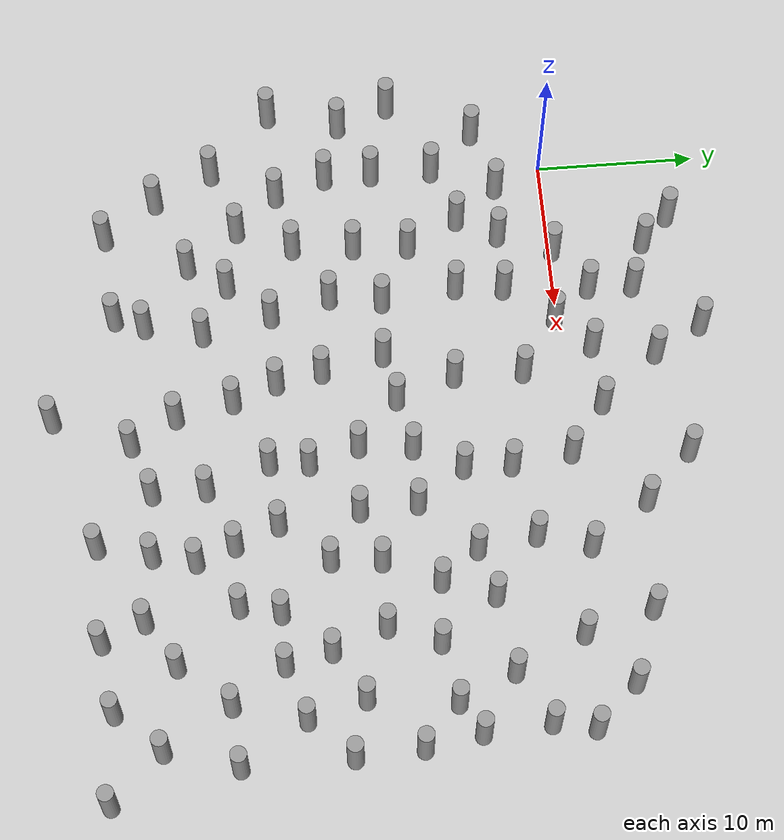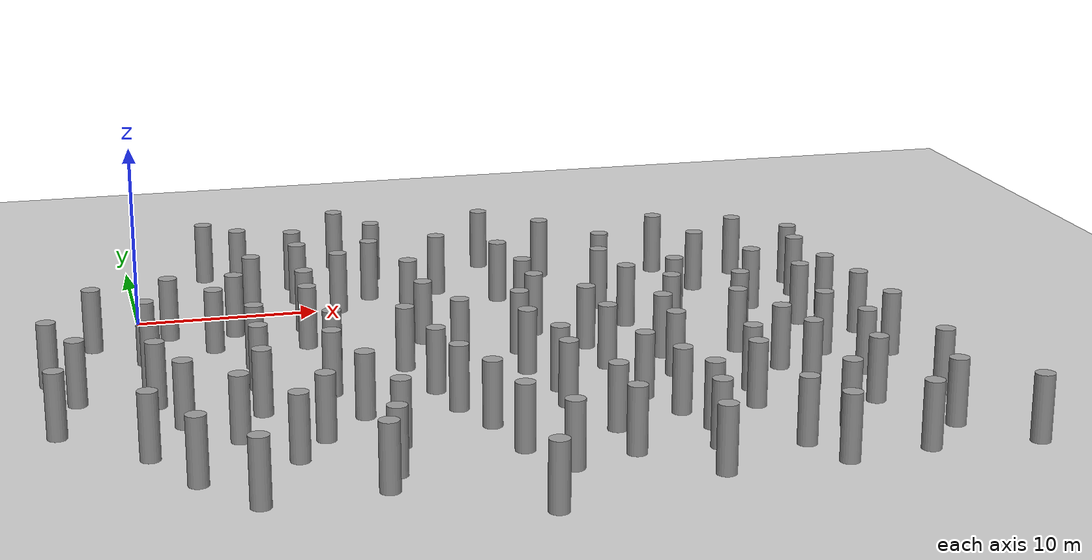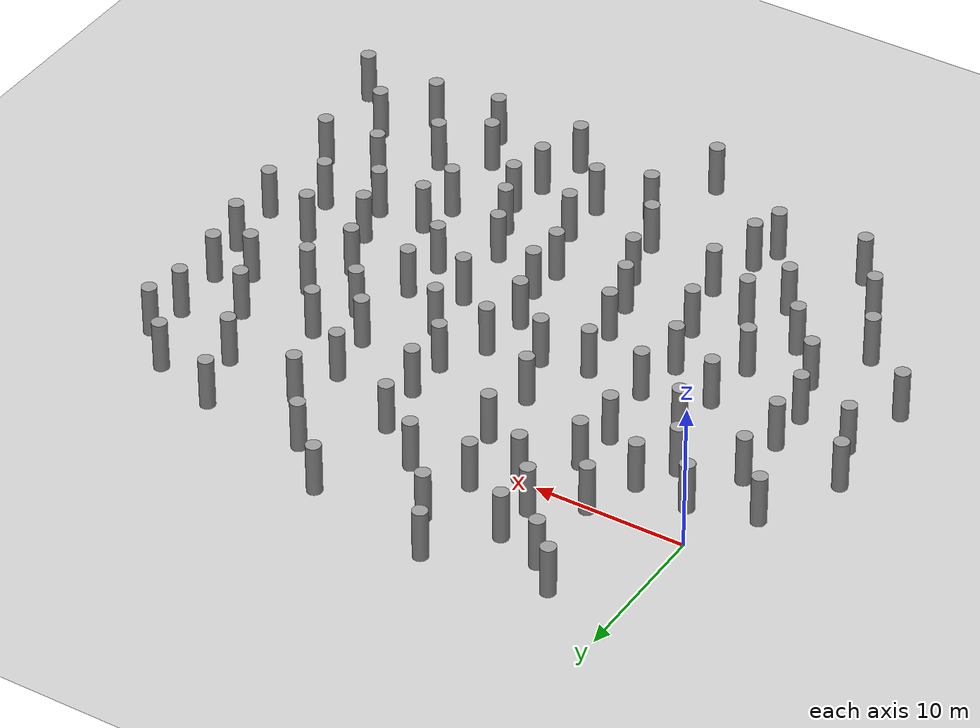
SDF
<sdf version="1.6">
 <world name="default">
  <physics name="default_physics" default="0" type="ode">
   <ode>
    <solver>
     <type>quick</type>
     <iters>100</iters>
     <sor>1</sor>
     <use_dynamic_moi_rescaling>0</use_dynamic_moi_rescaling>
    </solver>
    <constraints>
     <cfm>0</cfm>
     <erp>0.2</erp>
     <contact_max_correcting_vel>0.1</contact_max_correcting_vel>
     <contact_surface_layer>0</contact_surface_layer>
    </constraints>
   </ode>
   <real_time_update_rate>-1</real_time_update_rate>
   <max_step_size>0.001</max_step_size>
   <real_time_factor>1</real_time_factor>
  </physics>
  <gravity>0 0 -9.8</gravity>
  <light name="sun" type="directional">
   <pose>0 0 10 0 -0 0</pose>
   <diffuse>0.8 0.8 0.8 1</diffuse>
   <specular>0.2 0.2 0.2 1</specular>
   <attenuation>
    <range>1000</range>
    <constant>0.9</constant>
    <linear>0.01</linear>
    <quadratic>0.001</quadratic>
   </attenuation>
   <direction>-0.5 0.1 -0.9</direction>
  </light>
  <model name="ground_plane">
   <static>1</static>
   <link name="link">
    <collision name="collision">
     <geometry><plane><normal>0 0 1</normal><size>5000 5000</size></plane></geometry>
     <surface><friction><ode><mu>1</mu><mu2>2</mu2></ode></friction></surface>
    </collision>
    <visual name="runway">
     <cast_shadows>0</cast_shadows>
     <geometry><plane><normal>0 0 1</normal><size>700 700</size></plane></geometry>
     <material>
      <script><uri>file://media/materials/scripts/gazebo.material</uri><name>Gazebo/Gray</name></script>
     </material>
    </visual>
   </link>
  </model>
  <magnetic_field>6e-06 2.3e-05 -4.2e-05</magnetic_field>
  <atmosphere type="adiabatic"/>
  <scene><ambient>0.4 0.4 0.4 1</ambient><background>0.7 0.7 0.7 1</background><shadows>1</shadows></scene>
  <spherical_coordinates>
   <surface_model>EARTH_WGS84</surface_model>
   <latitude_deg>0</latitude_deg>
   <longitude_deg>0</longitude_deg>
   <elevation>0</elevation>
   <heading_deg>0</heading_deg>
  </spherical_coordinates>
  <model name="unit_cylinder_clone_0_clone">
   <link name="link">
    <inertial>
     <mass>1</mass>
     <inertia><ixx>0.145833</ixx><ixy>0</ixy><ixz>0</ixz><iyy>0.145833</iyy><iyz>0</iyz><izz>0.125</izz></inertia>
    </inertial>
    <gravity>0</gravity>
    <visual name="visual">
     <geometry><cylinder><radius>0.5</radius><length>3.42215</length></cylinder></geometry>
     <material>
      <script><name>Gazebo/Grey</name><uri>file://media/materials/scripts/gazebo.material</uri></script>
      <shader type="pixel"><normal_map>__default__</normal_map></shader>
     </material>
    </visual>
   </link>
   <static>0</static>
   <pose>6.42186 0.174639 1.71107 0 0 -0.000115</pose>
  </model>
  <model name="unit_cylinder_clone_0_clone_clone">
   <link name="link">
    <inertial>
     <mass>1</mass>
     <inertia><ixx>0.145833</ixx><ixy>0</ixy><ixz>0</ixz><iyy>0.145833</iyy><iyz>0</iyz><izz>0.125</izz></inertia>
    </inertial>
    <gravity>0</gravity>
    <visual name="visual">
     <geometry><cylinder><radius>0.5</radius><length>3.42215</length></cylinder></geometry>
     <material>
      <script><name>Gazebo/Grey</name><uri>file://media/materials/scripts/gazebo.material</uri></script>
      <shader type="pixel"><normal_map>__default__</normal_map></shader>
     </material>
    </visual>
   </link>
   <static>0</static>
   <pose>8.93174 -3.18169 1.71107 0 0 -0.000115</pose>
  </model>
  <model name="unit_cylinder_clone_0_clone_clone_0">
   <link name="link">
    <inertial>
     <mass>1</mass>
     <inertia><ixx>0.145833</ixx><ixy>0</ixy><ixz>0</ixz><iyy>0.145833</iyy><iyz>0</iyz><izz>0.125</izz></inertia>
    </inertial>
    <gravity>0</gravity>
    <visual name="visual">
     <geometry><cylinder><radius>0.5</radius><length>3.42215</length></cylinder></geometry>
     <material>
      <script><name>Gazebo/Grey</name><uri>file://media/materials/scripts/gazebo.material</uri></script>
      <shader type="pixel"><normal_map>__default__</normal_map></shader>
     </material>
    </visual>
   </link>
   <static>0</static>
   <pose>9.28561 2.13063 1.71107 0 0 -0.000115</pose>
  </model>
  <model name="unit_cylinder_clone_0_clone_clone_1">
   <link name="link">
    <inertial>
     <mass>1</mass>
     <inertia><ixx>0.145833</ixx><ixy>0</ixy><ixz>0</ixz><iyy>0.145833</iyy><iyz>0</iyz><izz>0.125</izz></inertia>
    </inertial>
    <gravity>0</gravity>
    <visual name="visual">
     <geometry><cylinder><radius>0.5</radius><length>3.42215</length></cylinder></geometry>
     <material>
      <script><name>Gazebo/Grey</name><uri>file://media/materials/scripts/gazebo.material</uri></script>
      <shader type="pixel"><normal_map>__default__</normal_map></shader>
     </material>
    </visual>
   </link>
   <static>0</static>
   <pose>13.4104 1.91654 1.71107 0 0 -0.000115</pose>
  </model>
  <model name="unit_cylinder_clone_0_clone_clone_2">
   <link name="link">
    <inertial>
     <mass>1</mass>
     <inertia><ixx>0.145833</ixx><ixy>0</ixy><ixz>0</ixz><iyy>0.145833</iyy><iyz>0</iyz><izz>0.125</izz></inertia>
    </inertial>
    <gravity>0</gravity>
    <visual name="visual">
     <geometry><cylinder><radius>0.5</radius><length>3.42215</length></cylinder></geometry>
     <material>
      <script><name>Gazebo/Grey</name><uri>file://media/materials/scripts/gazebo.material</uri></script>
      <shader type="pixel"><normal_map>__default__</normal_map></shader>
     </material>
    </visual>
   </link>
   <static>0</static>
   <pose>9.37097 4.93335 1.71107 0 0 -0.000115</pose>
  </model>
  <model name="unit_cylinder_clone_0_clone_clone_3">
   <link name="link">
    <inertial>
     <mass>1</mass>
     <inertia><ixx>0.145833</ixx><ixy>0</ixy><ixz>0</ixz><iyy>0.145833</iyy><iyz>0</iyz><izz>0.125</izz></inertia>
    </inertial>
    <gravity>0</gravity>
    <visual name="visual">
     <geometry><cylinder><radius>0.5</radius><length>3.42215</length></cylinder></geometry>
     <material>
      <script><name>Gazebo/Grey</name><uri>file://media/materials/scripts/gazebo.material</uri></script>
      <shader type="pixel"><normal_map>__default__</normal_map></shader>
     </material>
    </visual>
   </link>
   <static>0</static>
   <pose>14.1844 5.78773 1.71107 0 0 -0.000115</pose>
  </model>
  <model name="unit_cylinder_clone_0_clone_clone_4">
   <link name="link">
    <inertial>
     <mass>1</mass>
     <inertia><ixx>0.145833</ixx><ixy>0</ixy><ixz>0</ixz><iyy>0.145833</iyy><iyz>0</iyz><izz>0.125</izz></inertia>
    </inertial>
    <gravity>0</gravity>
    <visual name="visual">
     <geometry><cylinder><radius>0.5</radius><length>3.42215</length></cylinder></geometry>
     <material>
      <script><name>Gazebo/Grey</name><uri>file://media/materials/scripts/gazebo.material</uri></script>
      <shader type="pixel"><normal_map>__default__</normal_map></shader>
     </material>
    </visual>
   </link>
   <static>0</static>
   <pose>14.8696 -2.51989 1.71107 0 0 -0.000115</pose>
  </model>
  <model name="unit_cylinder_clone_0_clone_clone_5">
   <link name="link">
    <inertial>
     <mass>1</mass>
     <inertia><ixx>0.145833</ixx><ixy>0</ixy><ixz>0</ixz><iyy>0.145833</iyy><iyz>0</iyz><izz>0.125</izz></inertia>
    </inertial>
    <gravity>0</gravity>
    <visual name="visual">
     <geometry><cylinder><radius>0.5</radius><length>3.42215</length></cylinder></geometry>
     <material>
      <script><name>Gazebo/Grey</name><uri>file://media/materials/scripts/gazebo.material</uri></script>
      <shader type="pixel"><normal_map>__default__</normal_map></shader>
     </material>
    </visual>
   </link>
   <static>0</static>
   <pose>14.8701 -6.8123 1.71107 0 0 -0.000115</pose>
  </model>
  <model name="unit_cylinder_clone_0_clone_clone_6">
   <link name="link">
    <inertial>
     <mass>1</mass>
     <inertia><ixx>0.145833</ixx><ixy>0</ixy><ixz>0</ixz><iyy>0.145833</iyy><iyz>0</iyz><izz>0.125</izz></inertia>
    </inertial>
    <gravity>0</gravity>
    <visual name="visual">
     <geometry><cylinder><radius>0.5</radius><length>3.42215</length></cylinder></geometry>
     <material>
      <script><name>Gazebo/Grey</name><uri>file://media/materials/scripts/gazebo.material</uri></script>
      <shader type="pixel"><normal_map>__default__</normal_map></shader>
     </material>
    </visual>
   </link>
   <static>0</static>
   <pose>8.6708 -6.19269 1.71107 0 0 -0.000115</pose>
  </model>
  <model name="unit_cylinder_clone_0_clone_clone_7">
   <link name="link">
    <inertial>
     <mass>1</mass>
     <inertia><ixx>0.145833</ixx><ixy>0</ixy><ixz>0</ixz><iyy>0.145833</iyy><iyz>0</iyz><izz>0.125</izz></inertia>
    </inertial>
    <gravity>0</gravity>
    <visual name="visual">
     <geometry><cylinder><radius>0.5</radius><length>3.42215</length></cylinder></geometry>
     <material>
      <script><name>Gazebo/Grey</name><uri>file://media/materials/scripts/gazebo.material</uri></script>
      <shader type="pixel"><normal_map>__default__</normal_map></shader>
     </material>
    </visual>
   </link>
   <static>0</static>
   <pose>11.2841 -0.175234 1.71107 0 0 -0.000115</pose>
  </model>
  <model name="unit_cylinder_clone_0_clone_clone_8">
   <link name="link">
    <inertial>
     <mass>1</mass>
     <inertia><ixx>0.145833</ixx><ixy>0</ixy><ixz>0</ixz><iyy>0.145833</iyy><iyz>0</iyz><izz>0.125</izz></inertia>
    </inertial>
    <gravity>0</gravity>
    <visual name="visual">
     <geometry><cylinder><radius>0.5</radius><length>3.42215</length></cylinder></geometry>
     <material>
      <script><name>Gazebo/Grey</name><uri>file://media/materials/scripts/gazebo.material</uri></script>
      <shader type="pixel"><normal_map>__default__</normal_map></shader>
     </material>
    </visual>
   </link>
   <static>0</static>
   <pose>20.5566 -0.116077 1.71107 0 0 -0.000115</pose>
  </model>
  <model name="unit_cylinder_clone_0_clone_clone_9">
   <link name="link">
    <inertial>
     <mass>1</mass>
     <inertia><ixx>0.145833</ixx><ixy>0</ixy><ixz>0</ixz><iyy>0.145833</iyy><iyz>0</iyz><izz>0.125</izz></inertia>
    </inertial>
    <gravity>0</gravity>
    <visual name="visual">
     <geometry><cylinder><radius>0.5</radius><length>3.42215</length></cylinder></geometry>
     <material>
      <script><name>Gazebo/Grey</name><uri>file://media/materials/scripts/gazebo.material</uri></script>
      <shader type="pixel"><normal_map>__default__</normal_map></shader>
     </material>
    </visual>
   </link>
   <static>0</static>
   <pose>17.3993 2.13427 1.71107 0 0 -0.000115</pose>
  </model>
  <model name="unit_cylinder_clone_0_clone_clone_10">
   <link name="link">
    <inertial>
     <mass>1</mass>
     <inertia><ixx>0.145833</ixx><ixy>0</ixy><ixz>0</ixz><iyy>0.145833</iyy><iyz>0</iyz><izz>0.125</izz></inertia>
    </inertial>
    <gravity>0</gravity>
    <visual name="visual">
     <geometry><cylinder><radius>0.5</radius><length>3.42215</length></cylinder></geometry>
     <material>
      <script><name>Gazebo/Grey</name><uri>file://media/materials/scripts/gazebo.material</uri></script>
      <shader type="pixel"><normal_map>__default__</normal_map></shader>
     </material>
    </visual>
   </link>
   <static>0</static>
   <pose>25.8377 -2.81658 1.71107 0 0 -0.000115</pose>
  </model>
  <model name="unit_cylinder_clone_0_clone_clone_11">
   <link name="link">
    <inertial>
     <mass>1</mass>
     <inertia><ixx>0.145833</ixx><ixy>0</ixy><ixz>0</ixz><iyy>0.145833</iyy><iyz>0</iyz><izz>0.125</izz></inertia>
    </inertial>
    <gravity>0</gravity>
    <visual name="visual">
     <geometry><cylinder><radius>0.5</radius><length>3.42215</length></cylinder></geometry>
     <material>
      <script><name>Gazebo/Grey</name><uri>file://media/materials/scripts/gazebo.material</uri></script>
      <shader type="pixel"><normal_map>__default__</normal_map></shader>
     </material>
    </visual>
   </link>
   <static>0</static>
   <pose>21.0532 -6.77808 1.71107 0 0 -0.000115</pose>
  </model>
  <model name="unit_cylinder_clone_0_clone_clone_12">
   <link name="link">
    <inertial>
     <mass>1</mass>
     <inertia><ixx>0.145833</ixx><ixy>0</ixy><ixz>0</ixz><iyy>0.145833</iyy><iyz>0</iyz><izz>0.125</izz></inertia>
    </inertial>
    <gravity>0</gravity>
    <visual name="visual">
     <geometry><cylinder><radius>0.5</radius><length>3.42215</length></cylinder></geometry>
     <material>
      <script><name>Gazebo/Grey</name><uri>file://media/materials/scripts/gazebo.material</uri></script>
      <shader type="pixel"><normal_map>__default__</normal_map></shader>
     </material>
    </visual>
   </link>
   <static>0</static>
   <pose>32.2475 -0.639695 1.71107 0 0 -0.000115</pose>
  </model>
  <model name="unit_cylinder_clone_0_clone_clone_13">
   <link name="link">
    <inertial>
     <mass>1</mass>
     <inertia><ixx>0.145833</ixx><ixy>0</ixy><ixz>0</ixz><iyy>0.145833</iyy><iyz>0</iyz><izz>0.125</izz></inertia>
    </inertial>
    <gravity>0</gravity>
    <visual name="visual">
     <geometry><cylinder><radius>0.5</radius><length>3.42215</length></cylinder></geometry>
     <material>
      <script><name>Gazebo/Grey</name><uri>file://media/materials/scripts/gazebo.material</uri></script>
      <shader type="pixel"><normal_map>__default__</normal_map></shader>
     </material>
    </visual>
   </link>
   <static>0</static>
   <pose>26.7729 0.402254 1.71107 0 0 -0.000115</pose>
  </model>
  <model name="unit_cylinder_clone_0_clone_clone_14">
   <link name="link">
    <inertial>
     <mass>1</mass>
     <inertia><ixx>0.145833</ixx><ixy>0</ixy><ixz>0</ixz><iyy>0.145833</iyy><iyz>0</iyz><izz>0.125</izz></inertia>
    </inertial>
    <gravity>0</gravity>
    <visual name="visual">
     <geometry><cylinder><radius>0.5</radius><length>3.42215</length></cylinder></geometry>
     <material>
      <script><name>Gazebo/Grey</name><uri>file://media/materials/scripts/gazebo.material</uri></script>
      <shader type="pixel"><normal_map>__default__</normal_map></shader>
     </material>
    </visual>
   </link>
   <static>0</static>
   <pose>24.07 4.06268 1.71107 0 0 -0.000115</pose>
  </model>
  <model name="unit_cylinder_clone_0_clone_clone_15">
   <link name="link">
    <inertial>
     <mass>1</mass>
     <inertia><ixx>0.145833</ixx><ixy>0</ixy><ixz>0</ixz><iyy>0.145833</iyy><iyz>0</iyz><izz>0.125</izz></inertia>
    </inertial>
    <gravity>0</gravity>
    <visual name="visual">
     <geometry><cylinder><radius>0.5</radius><length>3.42215</length></cylinder></geometry>
     <material>
      <script><name>Gazebo/Grey</name><uri>file://media/materials/scripts/gazebo.material</uri></script>
      <shader type="pixel"><normal_map>__default__</normal_map></shader>
     </material>
    </visual>
   </link>
   <static>0</static>
   <pose>31 3.55903 1.71107 0 0 -0.000115</pose>
  </model>
  <model name="unit_cylinder_clone_0_clone_clone_16">
   <link name="link">
    <inertial>
     <mass>1</mass>
     <inertia><ixx>0.145833</ixx><ixy>0</ixy><ixz>0</ixz><iyy>0.145833</iyy><iyz>0</iyz><izz>0.125</izz></inertia>
    </inertial>
    <gravity>0</gravity>
    <visual name="visual">
     <geometry><cylinder><radius>0.5</radius><length>3.42215</length></cylinder></geometry>
     <material>
      <script><name>Gazebo/Grey</name><uri>file://media/materials/scripts/gazebo.material</uri></script>
      <shader type="pixel"><normal_map>__default__</normal_map></shader>
     </material>
    </visual>
   </link>
   <static>0</static>
   <pose>21 7 1.71107 0 0 -0.000115</pose>
  </model>
  <model name="unit_cylinder_clone_0_clone_clone_17">
   <link name="link">
    <inertial>
     <mass>1</mass>
     <inertia><ixx>0.145833</ixx><ixy>0</ixy><ixz>0</ixz><iyy>0.145833</iyy><iyz>0</iyz><izz>0.125</izz></inertia>
    </inertial>
    <gravity>0</gravity>
    <visual name="visual">
     <geometry><cylinder><radius>0.5</radius><length>3.42215</length></cylinder></geometry>
     <material>
      <script><name>Gazebo/Grey</name><uri>file://media/materials/scripts/gazebo.material</uri></script>
      <shader type="pixel"><normal_map>__default__</normal_map></shader>
     </material>
    </visual>
   </link>
   <static>0</static>
   <pose>35.4755 1.99846 1.71107 0 0 -0.000115</pose>
  </model>
  <model name="unit_cylinder_clone_0_clone_clone_18">
   <link name="link">
    <inertial>
     <mass>1</mass>
     <inertia><ixx>0.145833</ixx><ixy>0</ixy><ixz>0</ixz><iyy>0.145833</iyy><iyz>0</iyz><izz>0.125</izz></inertia>
    </inertial>
    <gravity>0</gravity>
    <visual name="visual">
     <geometry><cylinder><radius>0.5</radius><length>3.42215</length></cylinder></geometry>
     <material>
      <script><name>Gazebo/Grey</name><uri>file://media/materials/scripts/gazebo.material</uri></script>
      <shader type="pixel"><normal_map>__default__</normal_map></shader>
     </material>
    </visual>
   </link>
   <static>0</static>
   <pose>37.5335 -3.11037 1.71107 0 0 -0.000115</pose>
  </model>
  <model name="unit_cylinder_clone_0_clone_clone_19">
   <link name="link">
    <inertial>
     <mass>1</mass>
     <inertia><ixx>0.145833</ixx><ixy>0</ixy><ixz>0</ixz><iyy>0.145833</iyy><iyz>0</iyz><izz>0.125</izz></inertia>
    </inertial>
    <gravity>0</gravity>
    <visual name="visual">
     <geometry><cylinder><radius>0.5</radius><length>3.42215</length></cylinder></geometry>
     <material>
      <script><name>Gazebo/Grey</name><uri>file://media/materials/scripts/gazebo.material</uri></script>
      <shader type="pixel"><normal_map>__default__</normal_map></shader>
     </material>
    </visual>
   </link>
   <static>0</static>
   <pose>34.2685 -4.92029 1.71107 0 0 -0.000115</pose>
  </model>
  <model name="unit_cylinder_clone_0_clone_clone_20">
   <link name="link">
    <inertial>
     <mass>1</mass>
     <inertia><ixx>0.145833</ixx><ixy>0</ixy><ixz>0</ixz><iyy>0.145833</iyy><iyz>0</iyz><izz>0.125</izz></inertia>
    </inertial>
    <gravity>0</gravity>
    <visual name="visual">
     <geometry><cylinder><radius>0.5</radius><length>3.42215</length></cylinder></geometry>
     <material>
      <script><name>Gazebo/Grey</name><uri>file://media/materials/scripts/gazebo.material</uri></script>
      <shader type="pixel"><normal_map>__default__</normal_map></shader>
     </material>
    </visual>
   </link>
   <static>0</static>
   <pose>38.4674 -10.5798 1.71107 0 0 -0.000115</pose>
  </model>
  <model name="unit_cylinder_clone_0_clone_clone_21">
   <link name="link">
    <inertial>
     <mass>1</mass>
     <inertia><ixx>0.145833</ixx><ixy>0</ixy><ixz>0</ixz><iyy>0.145833</iyy><iyz>0</iyz><izz>0.125</izz></inertia>
    </inertial>
    <gravity>0</gravity>
    <visual name="visual">
     <geometry><cylinder><radius>0.5</radius><length>3.42215</length></cylinder></geometry>
     <material>
      <script><name>Gazebo/Grey</name><uri>file://media/materials/scripts/gazebo.material</uri></script>
      <shader type="pixel"><normal_map>__default__</normal_map></shader>
     </material>
    </visual>
   </link>
   <static>0</static>
   <pose>32.1445 -9.07488 1.71107 0 0 -0.000115</pose>
  </model>
  <model name="unit_cylinder_clone_0_clone_clone_22">
   <link name="link">
    <inertial>
     <mass>1</mass>
     <inertia><ixx>0.145833</ixx><ixy>0</ixy><ixz>0</ixz><iyy>0.145833</iyy><iyz>0</iyz><izz>0.125</izz></inertia>
    </inertial>
    <gravity>0</gravity>
    <visual name="visual">
     <geometry><cylinder><radius>0.5</radius><length>3.42215</length></cylinder></geometry>
     <material>
      <script><name>Gazebo/Grey</name><uri>file://media/materials/scripts/gazebo.material</uri></script>
      <shader type="pixel"><normal_map>__default__</normal_map></shader>
     </material>
    </visual>
   </link>
   <static>0</static>
   <pose>29.4758 -5.60259 1.71107 0 0 -0.000115</pose>
  </model>
  <model name="unit_cylinder_clone_0_clone_clone_23">
   <link name="link">
    <inertial>
     <mass>1</mass>
     <inertia><ixx>0.145833</ixx><ixy>0</ixy><ixz>0</ixz><iyy>0.145833</iyy><iyz>0</iyz><izz>0.125</izz></inertia>
    </inertial>
    <gravity>0</gravity>
    <visual name="visual">
     <geometry><cylinder><radius>0.5</radius><length>3.42215</length></cylinder></geometry>
     <material>
      <script><name>Gazebo/Grey</name><uri>file://media/materials/scripts/gazebo.material</uri></script>
      <shader type="pixel"><normal_map>__default__</normal_map></shader>
     </material>
    </visual>
   </link>
   <static>0</static>
   <pose>38.0442 -0.58433 1.71107 0 0 -0.000115</pose>
  </model>
  <model name="unit_cylinder_clone_0_clone_clone_24">
   <link name="link">
    <inertial>
     <mass>1</mass>
     <inertia><ixx>0.145833</ixx><ixy>0</ixy><ixz>0</ixz><iyy>0.145833</iyy><iyz>0</iyz><izz>0.125</izz></inertia>
    </inertial>
    <gravity>0</gravity>
    <visual name="visual">
     <geometry><cylinder><radius>0.5</radius><length>3.42215</length></cylinder></geometry>
     <material>
      <script><name>Gazebo/Grey</name><uri>file://media/materials/scripts/gazebo.material</uri></script>
      <shader type="pixel"><normal_map>__default__</normal_map></shader>
     </material>
    </visual>
   </link>
   <static>0</static>
   <pose>37.8456 -7.15705 1.71107 0 0 -0.000115</pose>
  </model>
  <model name="unit_cylinder_clone_0_clone_clone_25">
   <link name="link">
    <inertial>
     <mass>1</mass>
     <inertia><ixx>0.145833</ixx><ixy>0</ixy><ixz>0</ixz><iyy>0.145833</iyy><iyz>0</iyz><izz>0.125</izz></inertia>
    </inertial>
    <gravity>0</gravity>
    <visual name="visual">
     <geometry><cylinder><radius>0.5</radius><length>3.42215</length></cylinder></geometry>
     <material>
      <script><name>Gazebo/Grey</name><uri>file://media/materials/scripts/gazebo.material</uri></script>
      <shader type="pixel"><normal_map>__default__</normal_map></shader>
     </material>
    </visual>
   </link>
   <static>0</static>
   <pose>35.8829 -8.38323 1.71107 0 0 -0.000115</pose>
  </model>
  <model name="unit_cylinder_clone_0_clone_clone_26">
   <link name="link">
    <inertial>
     <mass>1</mass>
     <inertia><ixx>0.145833</ixx><ixy>0</ixy><ixz>0</ixz><iyy>0.145833</iyy><iyz>0</iyz><izz>0.125</izz></inertia>
    </inertial>
    <gravity>0</gravity>
    <visual name="visual">
     <geometry><cylinder><radius>0.5</radius><length>3.42215</length></cylinder></geometry>
     <material>
      <script><name>Gazebo/Grey</name><uri>file://media/materials/scripts/gazebo.material</uri></script>
      <shader type="pixel"><normal_map>__default__</normal_map></shader>
     </material>
    </visual>
   </link>
   <static>0</static>
   <pose>35.2555 -13.7054 1.71107 0 0 -0.000115</pose>
  </model>
  <model name="unit_cylinder_clone_0_clone_clone_27">
   <link name="link">
    <inertial>
     <mass>1</mass>
     <inertia><ixx>0.145833</ixx><ixy>0</ixy><ixz>0</ixz><iyy>0.145833</iyy><iyz>0</iyz><izz>0.125</izz></inertia>
    </inertial>
    <gravity>0</gravity>
    <visual name="visual">
     <geometry><cylinder><radius>0.5</radius><length>3.42215</length></cylinder></geometry>
     <material>
      <script><name>Gazebo/Grey</name><uri>file://media/materials/scripts/gazebo.material</uri></script>
      <shader type="pixel"><normal_map>__default__</normal_map></shader>
     </material>
    </visual>
   </link>
   <static>0</static>
   <pose>30.9358 -12.1807 1.71107 0 0 -0.000115</pose>
  </model>
  <model name="unit_cylinder_clone_0_clone_clone_28">
   <link name="link">
    <inertial>
     <mass>1</mass>
     <inertia><ixx>0.145833</ixx><ixy>0</ixy><ixz>0</ixz><iyy>0.145833</iyy><iyz>0</iyz><izz>0.125</izz></inertia>
    </inertial>
    <gravity>0</gravity>
    <visual name="visual">
     <geometry><cylinder><radius>0.5</radius><length>3.42215</length></cylinder></geometry>
     <material>
      <script><name>Gazebo/Grey</name><uri>file://media/materials/scripts/gazebo.material</uri></script>
      <shader type="pixel"><normal_map>__default__</normal_map></shader>
     </material>
    </visual>
   </link>
   <static>0</static>
   <pose>32.2011 -15.4854 1.71107 0 0 -0.000115</pose>
  </model>
  <model name="unit_cylinder_clone_0_clone_clone_29">
   <link name="link">
    <inertial>
     <mass>1</mass>
     <inertia><ixx>0.145833</ixx><ixy>0</ixy><ixz>0</ixz><iyy>0.145833</iyy><iyz>0</iyz><izz>0.125</izz></inertia>
    </inertial>
    <gravity>0</gravity>
    <visual name="visual">
     <geometry><cylinder><radius>0.5</radius><length>3.42215</length></cylinder></geometry>
     <material>
      <script><name>Gazebo/Grey</name><uri>file://media/materials/scripts/gazebo.material</uri></script>
      <shader type="pixel"><normal_map>__default__</normal_map></shader>
     </material>
    </visual>
   </link>
   <static>0</static>
   <pose>38.7271 -14.6175 1.71107 0 0 -0.000115</pose>
  </model>
  <model name="unit_cylinder_clone_0_clone_clone_30">
   <link name="link">
    <inertial>
     <mass>1</mass>
     <inertia><ixx>0.145833</ixx><ixy>0</ixy><ixz>0</ixz><iyy>0.145833</iyy><iyz>0</iyz><izz>0.125</izz></inertia>
    </inertial>
    <gravity>0</gravity>
    <visual name="visual">
     <geometry><cylinder><radius>0.5</radius><length>3.42215</length></cylinder></geometry>
     <material>
      <script><name>Gazebo/Grey</name><uri>file://media/materials/scripts/gazebo.material</uri></script>
      <shader type="pixel"><normal_map>__default__</normal_map></shader>
     </material>
    </visual>
   </link>
   <static>0</static>
   <pose>36.249 -17.2065 1.71107 0 0 -0.000115</pose>
  </model>
  <model name="unit_cylinder_clone_0_clone_clone_31">
   <link name="link">
    <inertial>
     <mass>1</mass>
     <inertia><ixx>0.145833</ixx><ixy>0</ixy><ixz>0</ixz><iyy>0.145833</iyy><iyz>0</iyz><izz>0.125</izz></inertia>
    </inertial>
    <gravity>0</gravity>
    <visual name="visual">
     <geometry><cylinder><radius>0.5</radius><length>3.42215</length></cylinder></geometry>
     <material>
      <script><name>Gazebo/Grey</name><uri>file://media/materials/scripts/gazebo.material</uri></script>
      <shader type="pixel"><normal_map>__default__</normal_map></shader>
     </material>
    </visual>
   </link>
   <static>0</static>
   <pose>28.3271 -8.74701 1.71107 0 0 -0.000115</pose>
  </model>
  <model name="unit_cylinder_clone_0_clone_clone_32">
   <link name="link">
    <inertial>
     <mass>1</mass>
     <inertia><ixx>0.145833</ixx><ixy>0</ixy><ixz>0</ixz><iyy>0.145833</iyy><iyz>0</iyz><izz>0.125</izz></inertia>
    </inertial>
    <gravity>0</gravity>
    <visual name="visual">
     <geometry><cylinder><radius>0.5</radius><length>3.42215</length></cylinder></geometry>
     <material>
      <script><name>Gazebo/Grey</name><uri>file://media/materials/scripts/gazebo.material</uri></script>
      <shader type="pixel"><normal_map>__default__</normal_map></shader>
     </material>
    </visual>
   </link>
   <static>0</static>
   <pose>26.4165 -6.41392 1.71107 0 0 -0.000115</pose>
  </model>
  <model name="unit_cylinder_clone_0_clone_clone_33">
   <link name="link">
    <inertial>
     <mass>1</mass>
     <inertia><ixx>0.145833</ixx><ixy>0</ixy><ixz>0</ixz><iyy>0.145833</iyy><iyz>0</iyz><izz>0.125</izz></inertia>
    </inertial>
    <gravity>0</gravity>
    <visual name="visual">
     <geometry><cylinder><radius>0.5</radius><length>3.42215</length></cylinder></geometry>
     <material>
      <script><name>Gazebo/Grey</name><uri>file://media/materials/scripts/gazebo.material</uri></script>
      <shader type="pixel"><normal_map>__default__</normal_map></shader>
     </material>
    </visual>
   </link>
   <static>0</static>
   <pose>32.8631 -18.2926 1.71107 0 0 -0.000115</pose>
  </model>
  <model name="unit_cylinder_clone_0_clone_clone_34">
   <link name="link">
    <inertial>
     <mass>1</mass>
     <inertia><ixx>0.145833</ixx><ixy>0</ixy><ixz>0</ixz><iyy>0.145833</iyy><iyz>0</iyz><izz>0.125</izz></inertia>
    </inertial>
    <gravity>0</gravity>
    <visual name="visual">
     <geometry><cylinder><radius>0.5</radius><length>3.42215</length></cylinder></geometry>
     <material>
      <script><name>Gazebo/Grey</name><uri>file://media/materials/scripts/gazebo.material</uri></script>
      <shader type="pixel"><normal_map>__default__</normal_map></shader>
     </material>
    </visual>
   </link>
   <static>0</static>
   <pose>38.8045 -21.2037 1.71107 0 0 -0.000115</pose>
  </model>
  <model name="unit_cylinder_clone_0_clone_clone_35">
   <link name="link">
    <inertial>
     <mass>1</mass>
     <inertia><ixx>0.145833</ixx><ixy>0</ixy><ixz>0</ixz><iyy>0.145833</iyy><iyz>0</iyz><izz>0.125</izz></inertia>
    </inertial>
    <gravity>0</gravity>
    <visual name="visual">
     <geometry><cylinder><radius>0.5</radius><length>3.42215</length></cylinder></geometry>
     <material>
      <script><name>Gazebo/Grey</name><uri>file://media/materials/scripts/gazebo.material</uri></script>
      <shader type="pixel"><normal_map>__default__</normal_map></shader>
     </material>
    </visual>
   </link>
   <static>0</static>
   <pose>35.0796 -21.5183 1.71107 0 0 -0.000115</pose>
  </model>
  <model name="unit_cylinder_clone_0_clone_clone_36">
   <link name="link">
    <inertial>
     <mass>1</mass>
     <inertia><ixx>0.145833</ixx><ixy>0</ixy><ixz>0</ixz><iyy>0.145833</iyy><iyz>0</iyz><izz>0.125</izz></inertia>
    </inertial>
    <gravity>0</gravity>
    <visual name="visual">
     <geometry><cylinder><radius>0.5</radius><length>3.42215</length></cylinder></geometry>
     <material>
      <script><name>Gazebo/Grey</name><uri>file://media/materials/scripts/gazebo.material</uri></script>
      <shader type="pixel"><normal_map>__default__</normal_map></shader>
     </material>
    </visual>
   </link>
   <static>0</static>
   <pose>37.5225 -25.6124 1.71107 0 0 -0.000115</pose>
  </model>
  <model name="unit_cylinder_clone_0_clone_clone_37">
   <link name="link">
    <inertial>
     <mass>1</mass>
     <inertia><ixx>0.145833</ixx><ixy>0</ixy><ixz>0</ixz><iyy>0.145833</iyy><iyz>0</iyz><izz>0.125</izz></inertia>
    </inertial>
    <gravity>0</gravity>
    <visual name="visual">
     <geometry><cylinder><radius>0.5</radius><length>3.42215</length></cylinder></geometry>
     <material>
      <script><name>Gazebo/Grey</name><uri>file://media/materials/scripts/gazebo.material</uri></script>
      <shader type="pixel"><normal_map>__default__</normal_map></shader>
     </material>
    </visual>
   </link>
   <static>0</static>
   <pose>32.4353 -24.5963 1.71107 0 0 -0.000115</pose>
  </model>
  <model name="unit_cylinder_clone_0_clone_clone_38">
   <link name="link">
    <inertial>
     <mass>1</mass>
     <inertia><ixx>0.145833</ixx><ixy>0</ixy><ixz>0</ixz><iyy>0.145833</iyy><iyz>0</iyz><izz>0.125</izz></inertia>
    </inertial>
    <gravity>0</gravity>
    <visual name="visual">
     <geometry><cylinder><radius>0.5</radius><length>3.42215</length></cylinder></geometry>
     <material>
      <script><name>Gazebo/Grey</name><uri>file://media/materials/scripts/gazebo.material</uri></script>
      <shader type="pixel"><normal_map>__default__</normal_map></shader>
     </material>
    </visual>
   </link>
   <static>0</static>
   <pose>29.018 -20.7801 1.71107 0 0 -0.000115</pose>
  </model>
  <model name="unit_cylinder_clone_0_clone_clone_39">
   <link name="link">
    <inertial>
     <mass>1</mass>
     <inertia><ixx>0.145833</ixx><ixy>0</ixy><ixz>0</ixz><iyy>0.145833</iyy><iyz>0</iyz><izz>0.125</izz></inertia>
    </inertial>
    <gravity>0</gravity>
    <visual name="visual">
     <geometry><cylinder><radius>0.5</radius><length>3.42215</length></cylinder></geometry>
     <material>
      <script><name>Gazebo/Grey</name><uri>file://media/materials/scripts/gazebo.material</uri></script>
      <shader type="pixel"><normal_map>__default__</normal_map></shader>
     </material>
    </visual>
   </link>
   <static>0</static>
   <pose>35.0216 -28.3657 1.71107 0 0 -0.000115</pose>
  </model>
  <model name="unit_cylinder_clone_0_clone_clone_40">
   <link name="link">
    <inertial>
     <mass>1</mass>
     <inertia><ixx>0.145833</ixx><ixy>0</ixy><ixz>0</ixz><iyy>0.145833</iyy><iyz>0</iyz><izz>0.125</izz></inertia>
    </inertial>
    <gravity>0</gravity>
    <visual name="visual">
     <geometry><cylinder><radius>0.5</radius><length>3.42215</length></cylinder></geometry>
     <material>
      <script><name>Gazebo/Grey</name><uri>file://media/materials/scripts/gazebo.material</uri></script>
      <shader type="pixel"><normal_map>__default__</normal_map></shader>
     </material>
    </visual>
   </link>
   <static>0</static>
   <pose>40.4627 -28.7053 1.71107 0 0 -0.000115</pose>
  </model>
  <model name="unit_cylinder_clone_0_clone_clone_41">
   <link name="link">
    <inertial>
     <mass>1</mass>
     <inertia><ixx>0.145833</ixx><ixy>0</ixy><ixz>0</ixz><iyy>0.145833</iyy><iyz>0</iyz><izz>0.125</izz></inertia>
    </inertial>
    <gravity>0</gravity>
    <visual name="visual">
     <geometry><cylinder><radius>0.5</radius><length>3.42215</length></cylinder></geometry>
     <material>
      <script><name>Gazebo/Grey</name><uri>file://media/materials/scripts/gazebo.material</uri></script>
      <shader type="pixel"><normal_map>__default__</normal_map></shader>
     </material>
    </visual>
   </link>
   <static>0</static>
   <pose>29.5475 -26.3741 1.71107 0 0 -0.000115</pose>
  </model>
  <model name="unit_cylinder_clone_0_clone_clone_42">
   <link name="link">
    <inertial>
     <mass>1</mass>
     <inertia><ixx>0.145833</ixx><ixy>0</ixy><ixz>0</ixz><iyy>0.145833</iyy><iyz>0</iyz><izz>0.125</izz></inertia>
    </inertial>
    <gravity>0</gravity>
    <visual name="visual">
     <geometry><cylinder><radius>0.5</radius><length>3.42215</length></cylinder></geometry>
     <material>
      <script><name>Gazebo/Grey</name><uri>file://media/materials/scripts/gazebo.material</uri></script>
      <shader type="pixel"><normal_map>__default__</normal_map></shader>
     </material>
    </visual>
   </link>
   <static>0</static>
   <pose>25.9562 -23.2089 1.71107 0 0 -0.000115</pose>
  </model>
  <model name="unit_cylinder_clone_0_clone_clone_43">
   <link name="link">
    <inertial>
     <mass>1</mass>
     <inertia><ixx>0.145833</ixx><ixy>0</ixy><ixz>0</ixz><iyy>0.145833</iyy><iyz>0</iyz><izz>0.125</izz></inertia>
    </inertial>
    <gravity>0</gravity>
    <visual name="visual">
     <geometry><cylinder><radius>0.5</radius><length>3.42215</length></cylinder></geometry>
     <material>
      <script><name>Gazebo/Grey</name><uri>file://media/materials/scripts/gazebo.material</uri></script>
      <shader type="pixel"><normal_map>__default__</normal_map></shader>
     </material>
    </visual>
   </link>
   <static>0</static>
   <pose>30.661 -28.9742 1.71107 0 0 -0.000115</pose>
  </model>
  <model name="unit_cylinder_clone_0_clone_clone_44">
   <link name="link">
    <inertial>
     <mass>1</mass>
     <inertia><ixx>0.145833</ixx><ixy>0</ixy><ixz>0</ixz><iyy>0.145833</iyy><iyz>0</iyz><izz>0.125</izz></inertia>
    </inertial>
    <gravity>0</gravity>
    <visual name="visual">
     <geometry><cylinder><radius>0.5</radius><length>3.42215</length></cylinder></geometry>
     <material>
      <script><name>Gazebo/Grey</name><uri>file://media/materials/scripts/gazebo.material</uri></script>
      <shader type="pixel"><normal_map>__default__</normal_map></shader>
     </material>
    </visual>
   </link>
   <static>0</static>
   <pose>29.6007 -18.3285 1.71107 0 0 -0.000115</pose>
  </model>
  <model name="unit_cylinder_clone_0_clone_clone_45">
   <link name="link">
    <inertial>
     <mass>1</mass>
     <inertia><ixx>0.145833</ixx><ixy>0</ixy><ixz>0</ixz><iyy>0.145833</iyy><iyz>0</iyz><izz>0.125</izz></inertia>
    </inertial>
    <gravity>0</gravity>
    <visual name="visual">
     <geometry><cylinder><radius>0.5</radius><length>3.42215</length></cylinder></geometry>
     <material>
      <script><name>Gazebo/Grey</name><uri>file://media/materials/scripts/gazebo.material</uri></script>
      <shader type="pixel"><normal_map>__default__</normal_map></shader>
     </material>
    </visual>
   </link>
   <static>0</static>
   <pose>26.5197 -15.216 1.71107 0 0 -0.000115</pose>
  </model>
  <model name="unit_cylinder_clone_0_clone_clone_46">
   <link name="link">
    <inertial>
     <mass>1</mass>
     <inertia><ixx>0.145833</ixx><ixy>0</ixy><ixz>0</ixz><iyy>0.145833</iyy><iyz>0</iyz><izz>0.125</izz></inertia>
    </inertial>
    <gravity>0</gravity>
    <visual name="visual">
     <geometry><cylinder><radius>0.5</radius><length>3.42215</length></cylinder></geometry>
     <material>
      <script><name>Gazebo/Grey</name><uri>file://media/materials/scripts/gazebo.material</uri></script>
      <shader type="pixel"><normal_map>__default__</normal_map></shader>
     </material>
    </visual>
   </link>
   <static>0</static>
   <pose>26.762 -12.1574 1.71107 0 0 -0.000115</pose>
  </model>
  <model name="unit_cylinder_clone_0_clone_clone_47">
   <link name="link">
    <inertial>
     <mass>1</mass>
     <inertia><ixx>0.145833</ixx><ixy>0</ixy><ixz>0</ixz><iyy>0.145833</iyy><iyz>0</iyz><izz>0.125</izz></inertia>
    </inertial>
    <gravity>0</gravity>
    <visual name="visual">
     <geometry><cylinder><radius>0.5</radius><length>3.42215</length></cylinder></geometry>
     <material>
      <script><name>Gazebo/Grey</name><uri>file://media/materials/scripts/gazebo.material</uri></script>
      <shader type="pixel"><normal_map>__default__</normal_map></shader>
     </material>
    </visual>
   </link>
   <static>0</static>
   <pose>23.2155 -9.72788 1.71107 0 0 -0.000115</pose>
  </model>
  <model name="unit_cylinder_clone_0_clone_clone_48">
   <link name="link">
    <inertial>
     <mass>1</mass>
     <inertia><ixx>0.145833</ixx><ixy>0</ixy><ixz>0</ixz><iyy>0.145833</iyy><iyz>0</iyz><izz>0.125</izz></inertia>
    </inertial>
    <gravity>0</gravity>
    <visual name="visual">
     <geometry><cylinder><radius>0.5</radius><length>3.42215</length></cylinder></geometry>
     <material>
      <script><name>Gazebo/Grey</name><uri>file://media/materials/scripts/gazebo.material</uri></script>
      <shader type="pixel"><normal_map>__default__</normal_map></shader>
     </material>
    </visual>
   </link>
   <static>0</static>
   <pose>21.1196 -3.84253 1.71107 0 0 -0.000115</pose>
  </model>
  <model name="unit_cylinder_clone_0_clone_clone_49">
   <link name="link">
    <inertial>
     <mass>1</mass>
     <inertia><ixx>0.145833</ixx><ixy>0</ixy><ixz>0</ixz><iyy>0.145833</iyy><iyz>0</iyz><izz>0.125</izz></inertia>
    </inertial>
    <gravity>0</gravity>
    <visual name="visual">
     <geometry><cylinder><radius>0.5</radius><length>3.42215</length></cylinder></geometry>
     <material>
      <script><name>Gazebo/Grey</name><uri>file://media/materials/scripts/gazebo.material</uri></script>
      <shader type="pixel"><normal_map>__default__</normal_map></shader>
     </material>
    </visual>
   </link>
   <static>0</static>
   <pose>19.5317 -9.74031 1.71107 0 0 -0.000115</pose>
  </model>
  <model name="unit_cylinder_clone_0_clone_clone_50">
   <link name="link">
    <inertial>
     <mass>1</mass>
     <inertia><ixx>0.145833</ixx><ixy>0</ixy><ixz>0</ixz><iyy>0.145833</iyy><iyz>0</iyz><izz>0.125</izz></inertia>
    </inertial>
    <gravity>0</gravity>
    <visual name="visual">
     <geometry><cylinder><radius>0.5</radius><length>3.42215</length></cylinder></geometry>
     <material>
      <script><name>Gazebo/Grey</name><uri>file://media/materials/scripts/gazebo.material</uri></script>
      <shader type="pixel"><normal_map>__default__</normal_map></shader>
     </material>
    </visual>
   </link>
   <static>0</static>
   <pose>23.413 -13.25 1.71107 0 0 -0.000115</pose>
  </model>
  <model name="unit_cylinder_clone_0_clone_clone_51">
   <link name="link">
    <inertial>
     <mass>1</mass>
     <inertia><ixx>0.145833</ixx><ixy>0</ixy><ixz>0</ixz><iyy>0.145833</iyy><iyz>0</iyz><izz>0.125</izz></inertia>
    </inertial>
    <gravity>0</gravity>
    <visual name="visual">
     <geometry><cylinder><radius>0.5</radius><length>3.42215</length></cylinder></geometry>
     <material>
      <script><name>Gazebo/Grey</name><uri>file://media/materials/scripts/gazebo.material</uri></script>
      <shader type="pixel"><normal_map>__default__</normal_map></shader>
     </material>
    </visual>
   </link>
   <static>0</static>
   <pose>23.9594 -18.1779 1.71107 0 0 -0.000115</pose>
  </model>
  <model name="unit_cylinder_clone_0_clone_clone_52">
   <link name="link">
    <inertial>
     <mass>1</mass>
     <inertia><ixx>0.145833</ixx><ixy>0</ixy><ixz>0</ixz><iyy>0.145833</iyy><iyz>0</iyz><izz>0.125</izz></inertia>
    </inertial>
    <gravity>0</gravity>
    <visual name="visual">
     <geometry><cylinder><radius>0.5</radius><length>3.42215</length></cylinder></geometry>
     <material>
      <script><name>Gazebo/Grey</name><uri>file://media/materials/scripts/gazebo.material</uri></script>
      <shader type="pixel"><normal_map>__default__</normal_map></shader>
     </material>
    </visual>
   </link>
   <static>0</static>
   <pose>25.0882 -20.8483 1.71107 0 0 -0.000115</pose>
  </model>
  <model name="unit_cylinder_clone_0_clone_clone_53">
   <link name="link">
    <inertial>
     <mass>1</mass>
     <inertia><ixx>0.145833</ixx><ixy>0</ixy><ixz>0</ixz><iyy>0.145833</iyy><iyz>0</iyz><izz>0.125</izz></inertia>
    </inertial>
    <gravity>0</gravity>
    <visual name="visual">
     <geometry><cylinder><radius>0.5</radius><length>3.42215</length></cylinder></geometry>
     <material>
      <script><name>Gazebo/Grey</name><uri>file://media/materials/scripts/gazebo.material</uri></script>
      <shader type="pixel"><normal_map>__default__</normal_map></shader>
     </material>
    </visual>
   </link>
   <static>0</static>
   <pose>25.4319 -25.813 1.71107 0 0 -0.000115</pose>
  </model>
  <model name="unit_cylinder_clone_0_clone_clone_54">
   <link name="link">
    <inertial>
     <mass>1</mass>
     <inertia><ixx>0.145833</ixx><ixy>0</ixy><ixz>0</ixz><iyy>0.145833</iyy><iyz>0</iyz><izz>0.125</izz></inertia>
    </inertial>
    <gravity>0</gravity>
    <visual name="visual">
     <geometry><cylinder><radius>0.5</radius><length>3.42215</length></cylinder></geometry>
     <material>
      <script><name>Gazebo/Grey</name><uri>file://media/materials/scripts/gazebo.material</uri></script>
      <shader type="pixel"><normal_map>__default__</normal_map></shader>
     </material>
    </visual>
   </link>
   <static>0</static>
   <pose>24.5936 -29.0875 1.71107 0 0 -0.000115</pose>
  </model>
  <model name="unit_cylinder_clone_0_clone_clone_55">
   <link name="link">
    <inertial>
     <mass>1</mass>
     <inertia><ixx>0.145833</ixx><ixy>0</ixy><ixz>0</ixz><iyy>0.145833</iyy><iyz>0</iyz><izz>0.125</izz></inertia>
    </inertial>
    <gravity>0</gravity>
    <visual name="visual">
     <geometry><cylinder><radius>0.5</radius><length>3.42215</length></cylinder></geometry>
     <material>
      <script><name>Gazebo/Grey</name><uri>file://media/materials/scripts/gazebo.material</uri></script>
      <shader type="pixel"><normal_map>__default__</normal_map></shader>
     </material>
    </visual>
   </link>
   <static>0</static>
   <pose>18.0249 -26.8343 1.71107 0 0 -0.000115</pose>
  </model>
  <model name="unit_cylinder_clone_0_clone_clone_56">
   <link name="link">
    <inertial>
     <mass>1</mass>
     <inertia><ixx>0.145833</ixx><ixy>0</ixy><ixz>0</ixz><iyy>0.145833</iyy><iyz>0</iyz><izz>0.125</izz></inertia>
    </inertial>
    <gravity>0</gravity>
    <visual name="visual">
     <geometry><cylinder><radius>0.5</radius><length>3.42215</length></cylinder></geometry>
     <material>
      <script><name>Gazebo/Grey</name><uri>file://media/materials/scripts/gazebo.material</uri></script>
      <shader type="pixel"><normal_map>__default__</normal_map></shader>
     </material>
    </visual>
   </link>
   <static>0</static>
   <pose>21.3444 -25.6763 1.71107 0 0 -0.000115</pose>
  </model>
  <model name="unit_cylinder_clone_0_clone_clone_57">
   <link name="link">
    <inertial>
     <mass>1</mass>
     <inertia><ixx>0.145833</ixx><ixy>0</ixy><ixz>0</ixz><iyy>0.145833</iyy><iyz>0</iyz><izz>0.125</izz></inertia>
    </inertial>
    <gravity>0</gravity>
    <visual name="visual">
     <geometry><cylinder><radius>0.5</radius><length>3.42215</length></cylinder></geometry>
     <material>
      <script><name>Gazebo/Grey</name><uri>file://media/materials/scripts/gazebo.material</uri></script>
      <shader type="pixel"><normal_map>__default__</normal_map></shader>
     </material>
    </visual>
   </link>
   <static>0</static>
   <pose>21.3515 -22.3974 1.71107 0 0 -0.000115</pose>
  </model>
  <model name="unit_cylinder_clone_0_clone_clone_58">
   <link name="link">
    <inertial>
     <mass>1</mass>
     <inertia><ixx>0.145833</ixx><ixy>0</ixy><ixz>0</ixz><iyy>0.145833</iyy><iyz>0</iyz><izz>0.125</izz></inertia>
    </inertial>
    <gravity>0</gravity>
    <visual name="visual">
     <geometry><cylinder><radius>0.5</radius><length>3.42215</length></cylinder></geometry>
     <material>
      <script><name>Gazebo/Grey</name><uri>file://media/materials/scripts/gazebo.material</uri></script>
      <shader type="pixel"><normal_map>__default__</normal_map></shader>
     </material>
    </visual>
   </link>
   <static>0</static>
   <pose>19.9196 -18.5137 1.71107 0 0 -0.000115</pose>
  </model>
  <model name="unit_cylinder_clone_0_clone_clone_59">
   <link name="link">
    <inertial>
     <mass>1</mass>
     <inertia><ixx>0.145833</ixx><ixy>0</ixy><ixz>0</ixz><iyy>0.145833</iyy><iyz>0</iyz><izz>0.125</izz></inertia>
    </inertial>
    <gravity>0</gravity>
    <visual name="visual">
     <geometry><cylinder><radius>0.5</radius><length>3.42215</length></cylinder></geometry>
     <material>
      <script><name>Gazebo/Grey</name><uri>file://media/materials/scripts/gazebo.material</uri></script>
      <shader type="pixel"><normal_map>__default__</normal_map></shader>
     </material>
    </visual>
   </link>
   <static>0</static>
   <pose>20.1209 -16.1005 1.71107 0 0 -0.000115</pose>
  </model>
  <model name="unit_cylinder_clone_0_clone_clone_60">
   <link name="link">
    <inertial>
     <mass>1</mass>
     <inertia><ixx>0.145833</ixx><ixy>0</ixy><ixz>0</ixz><iyy>0.145833</iyy><iyz>0</iyz><izz>0.125</izz></inertia>
    </inertial>
    <gravity>0</gravity>
    <visual name="visual">
     <geometry><cylinder><radius>0.5</radius><length>3.42215</length></cylinder></geometry>
     <material>
      <script><name>Gazebo/Grey</name><uri>file://media/materials/scripts/gazebo.material</uri></script>
      <shader type="pixel"><normal_map>__default__</normal_map></shader>
     </material>
    </visual>
   </link>
   <static>0</static>
   <pose>19.1624 -13.0304 1.71107 0 0 -0.000115</pose>
  </model>
  <model name="unit_cylinder_clone_0_clone_clone_61">
   <link name="link">
    <inertial>
     <mass>1</mass>
     <inertia><ixx>0.145833</ixx><ixy>0</ixy><ixz>0</ixz><iyy>0.145833</iyy><iyz>0</iyz><izz>0.125</izz></inertia>
    </inertial>
    <gravity>0</gravity>
    <visual name="visual">
     <geometry><cylinder><radius>0.5</radius><length>3.42215</length></cylinder></geometry>
     <material>
      <script><name>Gazebo/Grey</name><uri>file://media/materials/scripts/gazebo.material</uri></script>
      <shader type="pixel"><normal_map>__default__</normal_map></shader>
     </material>
    </visual>
   </link>
   <static>0</static>
   <pose>16.1323 -10.4661 1.71107 0 0 -0.000115</pose>
  </model>
  <model name="unit_cylinder_clone_0_clone_clone_62">
   <link name="link">
    <inertial>
     <mass>1</mass>
     <inertia><ixx>0.145833</ixx><ixy>0</ixy><ixz>0</ixz><iyy>0.145833</iyy><iyz>0</iyz><izz>0.125</izz></inertia>
    </inertial>
    <gravity>0</gravity>
    <visual name="visual">
     <geometry><cylinder><radius>0.5</radius><length>3.42215</length></cylinder></geometry>
     <material>
      <script><name>Gazebo/Grey</name><uri>file://media/materials/scripts/gazebo.material</uri></script>
      <shader type="pixel"><normal_map>__default__</normal_map></shader>
     </material>
    </visual>
   </link>
   <static>0</static>
   <pose>16.3551 -24.0548 1.71107 0 0 -0.000115</pose>
  </model>
  <model name="unit_cylinder_clone_0_clone_clone_63">
   <link name="link">
    <inertial>
     <mass>1</mass>
     <inertia><ixx>0.145833</ixx><ixy>0</ixy><ixz>0</ixz><iyy>0.145833</iyy><iyz>0</iyz><izz>0.125</izz></inertia>
    </inertial>
    <gravity>0</gravity>
    <visual name="visual">
     <geometry><cylinder><radius>0.5</radius><length>3.42215</length></cylinder></geometry>
     <material>
      <script><name>Gazebo/Grey</name><uri>file://media/materials/scripts/gazebo.material</uri></script>
      <shader type="pixel"><normal_map>__default__</normal_map></shader>
     </material>
    </visual>
   </link>
   <static>0</static>
   <pose>15.5957 -20.5049 1.71107 0 0 -0.000115</pose>
  </model>
  <model name="unit_cylinder_clone_0_clone_clone_64">
   <link name="link">
    <inertial>
     <mass>1</mass>
     <inertia><ixx>0.145833</ixx><ixy>0</ixy><ixz>0</ixz><iyy>0.145833</iyy><iyz>0</iyz><izz>0.125</izz></inertia>
    </inertial>
    <gravity>0</gravity>
    <visual name="visual">
     <geometry><cylinder><radius>0.5</radius><length>3.42215</length></cylinder></geometry>
     <material>
      <script><name>Gazebo/Grey</name><uri>file://media/materials/scripts/gazebo.material</uri></script>
      <shader type="pixel"><normal_map>__default__</normal_map></shader>
     </material>
    </visual>
   </link>
   <static>0</static>
   <pose>13.9463 -14.9316 1.71107 0 0 -0.000115</pose>
  </model>
  <model name="unit_cylinder_clone_0_clone_clone_65">
   <link name="link">
    <inertial>
     <mass>1</mass>
     <inertia><ixx>0.145833</ixx><ixy>0</ixy><ixz>0</ixz><iyy>0.145833</iyy><iyz>0</iyz><izz>0.125</izz></inertia>
    </inertial>
    <gravity>0</gravity>
    <visual name="visual">
     <geometry><cylinder><radius>0.5</radius><length>3.42215</length></cylinder></geometry>
     <material>
      <script><name>Gazebo/Grey</name><uri>file://media/materials/scripts/gazebo.material</uri></script>
      <shader type="pixel"><normal_map>__default__</normal_map></shader>
     </material>
    </visual>
   </link>
   <static>0</static>
   <pose>9.82236 -17.8402 1.71107 0 0 -0.000115</pose>
  </model>
  <model name="unit_cylinder_clone_0_clone_clone_66">
   <link name="link">
    <inertial>
     <mass>1</mass>
     <inertia><ixx>0.145833</ixx><ixy>0</ixy><ixz>0</ixz><iyy>0.145833</iyy><iyz>0</iyz><izz>0.125</izz></inertia>
    </inertial>
    <gravity>0</gravity>
    <visual name="visual">
     <geometry><cylinder><radius>0.5</radius><length>3.42215</length></cylinder></geometry>
     <material>
      <script><name>Gazebo/Grey</name><uri>file://media/materials/scripts/gazebo.material</uri></script>
      <shader type="pixel"><normal_map>__default__</normal_map></shader>
     </material>
    </visual>
   </link>
   <static>0</static>
   <pose>10.8062 -22.1559 1.71107 0 0 -0.000115</pose>
  </model>
  <model name="unit_cylinder_clone_0_clone_clone_67">
   <link name="link">
    <inertial>
     <mass>1</mass>
     <inertia><ixx>0.145833</ixx><ixy>0</ixy><ixz>0</ixz><iyy>0.145833</iyy><iyz>0</iyz><izz>0.125</izz></inertia>
    </inertial>
    <gravity>0</gravity>
    <visual name="visual">
     <geometry><cylinder><radius>0.5</radius><length>3.42215</length></cylinder></geometry>
     <material>
      <script><name>Gazebo/Grey</name><uri>file://media/materials/scripts/gazebo.material</uri></script>
      <shader type="pixel"><normal_map>__default__</normal_map></shader>
     </material>
    </visual>
   </link>
   <static>0</static>
   <pose>9.9642 -25.7558 1.71107 0 0 -0.000115</pose>
  </model>
  <model name="unit_cylinder_clone_0_clone_clone_68">
   <link name="link">
    <inertial>
     <mass>1</mass>
     <inertia><ixx>0.145833</ixx><ixy>0</ixy><ixz>0</ixz><iyy>0.145833</iyy><iyz>0</iyz><izz>0.125</izz></inertia>
    </inertial>
    <gravity>0</gravity>
    <visual name="visual">
     <geometry><cylinder><radius>0.5</radius><length>3.42215</length></cylinder></geometry>
     <material>
      <script><name>Gazebo/Grey</name><uri>file://media/materials/scripts/gazebo.material</uri></script>
      <shader type="pixel"><normal_map>__default__</normal_map></shader>
     </material>
    </visual>
   </link>
   <static>0</static>
   <pose>5.8935 -22.9119 1.71107 0 0 -0.000115</pose>
  </model>
  <model name="unit_cylinder_clone_0_clone_clone_69">
   <link name="link">
    <inertial>
     <mass>1</mass>
     <inertia><ixx>0.145833</ixx><ixy>0</ixy><ixz>0</ixz><iyy>0.145833</iyy><iyz>0</iyz><izz>0.125</izz></inertia>
    </inertial>
    <gravity>0</gravity>
    <visual name="visual">
     <geometry><cylinder><radius>0.5</radius><length>3.42215</length></cylinder></geometry>
     <material>
      <script><name>Gazebo/Grey</name><uri>file://media/materials/scripts/gazebo.material</uri></script>
      <shader type="pixel"><normal_map>__default__</normal_map></shader>
     </material>
    </visual>
   </link>
   <static>0</static>
   <pose>9.28829 -10.8592 1.71107 0 0 -0.000115</pose>
  </model>
  <model name="unit_cylinder_clone_0_clone_clone_70">
   <link name="link">
    <inertial>
     <mass>1</mass>
     <inertia><ixx>0.145833</ixx><ixy>0</ixy><ixz>0</ixz><iyy>0.145833</iyy><iyz>0</iyz><izz>0.125</izz></inertia>
    </inertial>
    <gravity>0</gravity>
    <visual name="visual">
     <geometry><cylinder><radius>0.5</radius><length>3.42215</length></cylinder></geometry>
     <material>
      <script><name>Gazebo/Grey</name><uri>file://media/materials/scripts/gazebo.material</uri></script>
      <shader type="pixel"><normal_map>__default__</normal_map></shader>
     </material>
    </visual>
   </link>
   <static>0</static>
   <pose>8.77797 -14.1287 1.71107 0 0 -0.000115</pose>
  </model>
  <model name="unit_cylinder_clone_0_clone_clone_71">
   <link name="link">
    <inertial>
     <mass>1</mass>
     <inertia><ixx>0.145833</ixx><ixy>0</ixy><ixz>0</ixz><iyy>0.145833</iyy><iyz>0</iyz><izz>0.125</izz></inertia>
    </inertial>
    <gravity>0</gravity>
    <visual name="visual">
     <geometry><cylinder><radius>0.5</radius><length>3.42215</length></cylinder></geometry>
     <material>
      <script><name>Gazebo/Grey</name><uri>file://media/materials/scripts/gazebo.material</uri></script>
      <shader type="pixel"><normal_map>__default__</normal_map></shader>
     </material>
    </visual>
   </link>
   <static>0</static>
   <pose>7.49045 -20.5014 1.71107 0 0 -0.000115</pose>
  </model>
  <model name="unit_cylinder_clone_0_clone_clone_72">
   <link name="link">
    <inertial>
     <mass>1</mass>
     <inertia><ixx>0.145833</ixx><ixy>0</ixy><ixz>0</ixz><iyy>0.145833</iyy><iyz>0</iyz><izz>0.125</izz></inertia>
    </inertial>
    <gravity>0</gravity>
    <visual name="visual">
     <geometry><cylinder><radius>0.5</radius><length>3.42215</length></cylinder></geometry>
     <material>
      <script><name>Gazebo/Grey</name><uri>file://media/materials/scripts/gazebo.material</uri></script>
      <shader type="pixel"><normal_map>__default__</normal_map></shader>
     </material>
    </visual>
   </link>
   <static>0</static>
   <pose>14.5206 -17.7966 1.71107 0 0 -0.000115</pose>
  </model>
  <model name="unit_cylinder_clone_0_clone_clone_73">
   <link name="link">
    <inertial>
     <mass>1</mass>
     <inertia><ixx>0.145833</ixx><ixy>0</ixy><ixz>0</ixz><iyy>0.145833</iyy><iyz>0</iyz><izz>0.125</izz></inertia>
    </inertial>
    <gravity>0</gravity>
    <visual name="visual">
     <geometry><cylinder><radius>0.5</radius><length>3.42215</length></cylinder></geometry>
     <material>
      <script><name>Gazebo/Grey</name><uri>file://media/materials/scripts/gazebo.material</uri></script>
      <shader type="pixel"><normal_map>__default__</normal_map></shader>
     </material>
    </visual>
   </link>
   <static>0</static>
   <pose>5.00571 -16.2365 1.71107 0 0 -0.000115</pose>
  </model>
  <model name="unit_cylinder_clone_0_clone_clone_74">
   <link name="link">
    <inertial>
     <mass>1</mass>
     <inertia><ixx>0.145833</ixx><ixy>0</ixy><ixz>0</ixz><iyy>0.145833</iyy><iyz>0</iyz><izz>0.125</izz></inertia>
    </inertial>
    <gravity>0</gravity>
    <visual name="visual">
     <geometry><cylinder><radius>0.5</radius><length>3.42215</length></cylinder></geometry>
     <material>
      <script><name>Gazebo/Grey</name><uri>file://media/materials/scripts/gazebo.material</uri></script>
      <shader type="pixel"><normal_map>__default__</normal_map></shader>
     </material>
    </visual>
   </link>
   <static>0</static>
   <pose>13.0824 -11.0732 1.71107 0 0 -0.000115</pose>
  </model>
  <model name="unit_cylinder_clone_0_clone_clone_75">
   <link name="link">
    <inertial>
     <mass>1</mass>
     <inertia><ixx>0.145833</ixx><ixy>0</ixy><ixz>0</ixz><iyy>0.145833</iyy><iyz>0</iyz><izz>0.125</izz></inertia>
    </inertial>
    <gravity>0</gravity>
    <visual name="visual">
     <geometry><cylinder><radius>0.5</radius><length>3.42215</length></cylinder></geometry>
     <material>
      <script><name>Gazebo/Grey</name><uri>file://media/materials/scripts/gazebo.material</uri></script>
      <shader type="pixel"><normal_map>__default__</normal_map></shader>
     </material>
    </visual>
   </link>
   <static>0</static>
   <pose>5.29371 -12.3858 1.71107 0 0 -0.000115</pose>
  </model>
  <model name="unit_cylinder_clone_0_clone_clone_76">
   <link name="link">
    <inertial>
     <mass>1</mass>
     <inertia><ixx>0.145833</ixx><ixy>0</ixy><ixz>0</ixz><iyy>0.145833</iyy><iyz>0</iyz><izz>0.125</izz></inertia>
    </inertial>
    <gravity>0</gravity>
    <visual name="visual">
     <geometry><cylinder><radius>0.5</radius><length>3.42215</length></cylinder></geometry>
     <material>
      <script><name>Gazebo/Grey</name><uri>file://media/materials/scripts/gazebo.material</uri></script>
      <shader type="pixel"><normal_map>__default__</normal_map></shader>
     </material>
    </visual>
   </link>
   <static>0</static>
   <pose>3.72444 -5.70004 1.71107 0 0 -0.000115</pose>
  </model>
  <model name="unit_cylinder_clone_0_clone_clone_77">
   <link name="link">
    <inertial>
     <mass>1</mass>
     <inertia><ixx>0.145833</ixx><ixy>0</ixy><ixz>0</ixz><iyy>0.145833</iyy><iyz>0</iyz><izz>0.125</izz></inertia>
    </inertial>
    <gravity>0</gravity>
    <visual name="visual">
     <geometry><cylinder><radius>0.5</radius><length>3.42215</length></cylinder></geometry>
     <material>
      <script><name>Gazebo/Grey</name><uri>file://media/materials/scripts/gazebo.material</uri></script>
      <shader type="pixel"><normal_map>__default__</normal_map></shader>
     </material>
    </visual>
   </link>
   <static>0</static>
   <pose>5.5007 -8.94298 1.71107 0 0 -0.000115</pose>
  </model>
  <model name="unit_cylinder_clone_0_clone_clone_78">
   <link name="link">
    <inertial>
     <mass>1</mass>
     <inertia><ixx>0.145833</ixx><ixy>0</ixy><ixz>0</ixz><iyy>0.145833</iyy><iyz>0</iyz><izz>0.125</izz></inertia>
    </inertial>
    <gravity>0</gravity>
    <visual name="visual">
     <geometry><cylinder><radius>0.5</radius><length>3.42215</length></cylinder></geometry>
     <material>
      <script><name>Gazebo/Grey</name><uri>file://media/materials/scripts/gazebo.material</uri></script>
      <shader type="pixel"><normal_map>__default__</normal_map></shader>
     </material>
    </visual>
   </link>
   <static>0</static>
   <pose>1.10693 -17.0797 1.71107 0 0 -0.000115</pose>
  </model>
  <model name="unit_cylinder_clone_0_clone_clone_79">
   <link name="link">
    <inertial>
     <mass>1</mass>
     <inertia><ixx>0.145833</ixx><ixy>0</ixy><ixz>0</ixz><iyy>0.145833</iyy><iyz>0</iyz><izz>0.125</izz></inertia>
    </inertial>
    <gravity>0</gravity>
    <visual name="visual">
     <geometry><cylinder><radius>0.5</radius><length>3.42215</length></cylinder></geometry>
     <material>
      <script><name>Gazebo/Grey</name><uri>file://media/materials/scripts/gazebo.material</uri></script>
      <shader type="pixel"><normal_map>__default__</normal_map></shader>
     </material>
    </visual>
   </link>
   <static>0</static>
   <pose>-0.86008 -21.1373 1.71107 0 0 -0.000115</pose>
  </model>
  <model name="unit_cylinder_clone_0_clone_clone_80">
   <link name="link">
    <inertial>
     <mass>1</mass>
     <inertia><ixx>0.145833</ixx><ixy>0</ixy><ixz>0</ixz><iyy>0.145833</iyy><iyz>0</iyz><izz>0.125</izz></inertia>
    </inertial>
    <gravity>0</gravity>
    <visual name="visual">
     <geometry><cylinder><radius>0.5</radius><length>3.42215</length></cylinder></geometry>
     <material>
      <script><name>Gazebo/Grey</name><uri>file://media/materials/scripts/gazebo.material</uri></script>
      <shader type="pixel"><normal_map>__default__</normal_map></shader>
     </material>
    </visual>
   </link>
   <static>0</static>
   <pose>1.01019 -24.8073 1.71107 0 0 -0.000115</pose>
  </model>
  <model name="unit_cylinder_clone_0_clone_clone_81">
   <link name="link">
    <inertial>
     <mass>1</mass>
     <inertia><ixx>0.145833</ixx><ixy>0</ixy><ixz>0</ixz><iyy>0.145833</iyy><iyz>0</iyz><izz>0.125</izz></inertia>
    </inertial>
    <gravity>0</gravity>
    <visual name="visual">
     <geometry><cylinder><radius>0.5</radius><length>3.42215</length></cylinder></geometry>
     <material>
      <script><name>Gazebo/Grey</name><uri>file://media/materials/scripts/gazebo.material</uri></script>
      <shader type="pixel"><normal_map>__default__</normal_map></shader>
     </material>
    </visual>
   </link>
   <static>0</static>
   <pose>3.42429 -28.0616 1.71107 0 0 -0.000115</pose>
  </model>
  <model name="unit_cylinder_clone_0_clone_clone_82">
   <link name="link">
    <inertial>
     <mass>1</mass>
     <inertia><ixx>0.145833</ixx><ixy>0</ixy><ixz>0</ixz><iyy>0.145833</iyy><iyz>0</iyz><izz>0.125</izz></inertia>
    </inertial>
    <gravity>0</gravity>
    <visual name="visual">
     <geometry><cylinder><radius>0.5</radius><length>3.42215</length></cylinder></geometry>
     <material>
      <script><name>Gazebo/Grey</name><uri>file://media/materials/scripts/gazebo.material</uri></script>
      <shader type="pixel"><normal_map>__default__</normal_map></shader>
     </material>
    </visual>
   </link>
   <static>0</static>
   <pose>9.26653 -27.6018 1.71107 0 0 -0.000115</pose>
  </model>
  <model name="unit_cylinder_clone_0_clone_clone_83">
   <link name="link">
    <inertial>
     <mass>1</mass>
     <inertia><ixx>0.145833</ixx><ixy>0</ixy><ixz>0</ixz><iyy>0.145833</iyy><iyz>0</iyz><izz>0.125</izz></inertia>
    </inertial>
    <gravity>0</gravity>
    <visual name="visual">
     <geometry><cylinder><radius>0.5</radius><length>3.42215</length></cylinder></geometry>
     <material>
      <script><name>Gazebo/Grey</name><uri>file://media/materials/scripts/gazebo.material</uri></script>
      <shader type="pixel"><normal_map>__default__</normal_map></shader>
     </material>
    </visual>
   </link>
   <static>0</static>
   <pose>16.029 -31.6017 1.71107 0 0 -0.000115</pose>
  </model>
  <model name="unit_cylinder_clone_0_clone_clone_84">
   <link name="link">
    <inertial>
     <mass>1</mass>
     <inertia><ixx>0.145833</ixx><ixy>0</ixy><ixz>0</ixz><iyy>0.145833</iyy><iyz>0</iyz><izz>0.125</izz></inertia>
    </inertial>
    <gravity>0</gravity>
    <visual name="visual">
     <geometry><cylinder><radius>0.5</radius><length>3.42215</length></cylinder></geometry>
     <material>
      <script><name>Gazebo/Grey</name><uri>file://media/materials/scripts/gazebo.material</uri></script>
      <shader type="pixel"><normal_map>__default__</normal_map></shader>
     </material>
    </visual>
   </link>
   <static>0</static>
   <pose>3.50523 -19.6975 1.71107 0 0 -0.000115</pose>
  </model>
  <model name="unit_cylinder_clone_0_clone_clone_85">
   <link name="link">
    <inertial>
     <mass>1</mass>
     <inertia><ixx>0.145833</ixx><ixy>0</ixy><ixz>0</ixz><iyy>0.145833</iyy><iyz>0</iyz><izz>0.125</izz></inertia>
    </inertial>
    <gravity>0</gravity>
    <visual name="visual">
     <geometry><cylinder><radius>0.5</radius><length>3.42215</length></cylinder></geometry>
     <material>
      <script><name>Gazebo/Grey</name><uri>file://media/materials/scripts/gazebo.material</uri></script>
      <shader type="pixel"><normal_map>__default__</normal_map></shader>
     </material>
    </visual>
   </link>
   <static>0</static>
   <pose>0.019225 -13.8729 1.71107 0 0 -0.000115</pose>
  </model>
  <model name="unit_cylinder_clone_0_clone_clone_86">
   <link name="link">
    <inertial>
     <mass>1</mass>
     <inertia><ixx>0.145833</ixx><ixy>0</ixy><ixz>0</ixz><iyy>0.145833</iyy><iyz>0</iyz><izz>0.125</izz></inertia>
    </inertial>
    <gravity>0</gravity>
    <visual name="visual">
     <geometry><cylinder><radius>0.5</radius><length>3.42215</length></cylinder></geometry>
     <material>
      <script><name>Gazebo/Grey</name><uri>file://media/materials/scripts/gazebo.material</uri></script>
      <shader type="pixel"><normal_map>__default__</normal_map></shader>
     </material>
    </visual>
   </link>
   <static>0</static>
   <pose>0 -7 1.71107 0 0 -0.000115</pose>
  </model>
  <model name="unit_cylinder_clone_0_clone_clone_87">
   <link name="link">
    <inertial>
     <mass>1</mass>
     <inertia><ixx>0.145833</ixx><ixy>0</ixy><ixz>0</ixz><iyy>0.145833</iyy><iyz>0</iyz><izz>0.125</izz></inertia>
    </inertial>
    <gravity>0</gravity>
    <visual name="visual">
     <geometry><cylinder><radius>0.5</radius><length>3.42215</length></cylinder></geometry>
     <material>
      <script><name>Gazebo/Grey</name><uri>file://media/materials/scripts/gazebo.material</uri></script>
      <shader type="pixel"><normal_map>__default__</normal_map></shader>
     </material>
    </visual>
   </link>
   <static>0</static>
   <pose>-4.96979 -17.2607 1.71107 0 0 -0.000115</pose>
  </model>
  <model name="unit_cylinder_clone_0_clone_clone_88">
   <link name="link">
    <inertial>
     <mass>1</mass>
     <inertia><ixx>0.145833</ixx><ixy>0</ixy><ixz>0</ixz><iyy>0.145833</iyy><iyz>0</iyz><izz>0.125</izz></inertia>
    </inertial>
    <gravity>0</gravity>
    <visual name="visual">
     <geometry><cylinder><radius>0.5</radius><length>3.42215</length></cylinder></geometry>
     <material>
      <script><name>Gazebo/Grey</name><uri>file://media/materials/scripts/gazebo.material</uri></script>
      <shader type="pixel"><normal_map>__default__</normal_map></shader>
     </material>
    </visual>
   </link>
   <static>0</static>
   <pose>-3.81934 -12.7714 1.71107 0 0 -0.000115</pose>
  </model>
  <model name="unit_cylinder_clone_0_clone_clone_89">
   <link name="link">
    <inertial>
     <mass>1</mass>
     <inertia><ixx>0.145833</ixx><ixy>0</ixy><ixz>0</ixz><iyy>0.145833</iyy><iyz>0</iyz><izz>0.125</izz></inertia>
    </inertial>
    <gravity>0</gravity>
    <visual name="visual">
     <geometry><cylinder><radius>0.5</radius><length>3.42215</length></cylinder></geometry>
     <material>
      <script><name>Gazebo/Grey</name><uri>file://media/materials/scripts/gazebo.material</uri></script>
      <shader type="pixel"><normal_map>__default__</normal_map></shader>
     </material>
    </visual>
   </link>
   <static>0</static>
   <pose>-0.015801 -10.8731 1.71107 0 0 -0.000115</pose>
  </model>
  <model name="unit_cylinder_clone_0_clone_clone_90">
   <link name="link">
    <inertial>
     <mass>1</mass>
     <inertia><ixx>0.145833</ixx><ixy>0</ixy><ixz>0</ixz><iyy>0.145833</iyy><iyz>0</iyz><izz>0.125</izz></inertia>
    </inertial>
    <gravity>0</gravity>
    <visual name="visual">
     <geometry><cylinder><radius>0.5</radius><length>3.42215</length></cylinder></geometry>
     <material>
      <script><name>Gazebo/Grey</name><uri>file://media/materials/scripts/gazebo.material</uri></script>
      <shader type="pixel"><normal_map>__default__</normal_map></shader>
     </material>
    </visual>
   </link>
   <static>0</static>
   <pose>-5.10137 -9.51203 1.71107 0 0 -0.000115</pose>
  </model>
  <model name="unit_cylinder_clone_0_clone_clone_91">
   <link name="link">
    <inertial>
     <mass>1</mass>
     <inertia><ixx>0.145833</ixx><ixy>0</ixy><ixz>0</ixz><iyy>0.145833</iyy><iyz>0</iyz><izz>0.125</izz></inertia>
    </inertial>
    <gravity>0</gravity>
    <visual name="visual">
     <geometry><cylinder><radius>0.5</radius><length>3.42215</length></cylinder></geometry>
     <material>
      <script><name>Gazebo/Grey</name><uri>file://media/materials/scripts/gazebo.material</uri></script>
      <shader type="pixel"><normal_map>__default__</normal_map></shader>
     </material>
    </visual>
   </link>
   <static>0</static>
   <pose>-2.61488 -4.19436 1.71107 0 0 -0.000115</pose>
  </model>
  <model name="unit_cylinder_clone_0_clone_clone_92">
   <link name="link">
    <inertial>
     <mass>1</mass>
     <inertia><ixx>0.145833</ixx><ixy>0</ixy><ixz>0</ixz><iyy>0.145833</iyy><iyz>0</iyz><izz>0.125</izz></inertia>
    </inertial>
    <gravity>0</gravity>
    <visual name="visual">
     <geometry><cylinder><radius>0.5</radius><length>3.42215</length></cylinder></geometry>
     <material>
      <script><name>Gazebo/Grey</name><uri>file://media/materials/scripts/gazebo.material</uri></script>
      <shader type="pixel"><normal_map>__default__</normal_map></shader>
     </material>
    </visual>
   </link>
   <static>0</static>
   <pose>1.54271 -3.01306 1.71107 0 0 -0.000115</pose>
  </model>
  <model name="unit_cylinder_clone_0_clone_clone_93">
   <link name="link">
    <inertial>
     <mass>1</mass>
     <inertia><ixx>0.145833</ixx><ixy>0</ixy><ixz>0</ixz><iyy>0.145833</iyy><iyz>0</iyz><izz>0.125</izz></inertia>
    </inertial>
    <gravity>0</gravity>
    <visual name="visual">
     <geometry><cylinder><radius>0.5</radius><length>3.42215</length></cylinder></geometry>
     <material>
      <script><name>Gazebo/Grey</name><uri>file://media/materials/scripts/gazebo.material</uri></script>
      <shader type="pixel"><normal_map>__default__</normal_map></shader>
     </material>
    </visual>
   </link>
   <static>0</static>
   <pose>5.08928 -3.18373 1.71107 0 0 -0.000115</pose>
  </model>
  <model name="unit_cylinder_clone_0_clone_clone_94">
   <link name="link">
    <inertial>
     <mass>1</mass>
     <inertia><ixx>0.145833</ixx><ixy>0</ixy><ixz>0</ixz><iyy>0.145833</iyy><iyz>0</iyz><izz>0.125</izz></inertia>
    </inertial>
    <gravity>0</gravity>
    <visual name="visual">
     <geometry><cylinder><radius>0.5</radius><length>3.42215</length></cylinder></geometry>
     <material>
      <script><name>Gazebo/Grey</name><uri>file://media/materials/scripts/gazebo.material</uri></script>
      <shader type="pixel"><normal_map>__default__</normal_map></shader>
     </material>
    </visual>
   </link>
   <static>0</static>
   <pose>4.48258 7.69524 1.71107 0 0 -0.000115</pose>
  </model>
  <model name="unit_cylinder_clone_0_clone_clone_95">
   <link name="link">
    <inertial>
     <mass>1</mass>
     <inertia><ixx>0.145833</ixx><ixy>0</ixy><ixz>0</ixz><iyy>0.145833</iyy><iyz>0</iyz><izz>0.125</izz></inertia>
    </inertial>
    <gravity>0</gravity>
    <visual name="visual">
     <geometry><cylinder><radius>0.5</radius><length>3.42215</length></cylinder></geometry>
     <material>
      <script><name>Gazebo/Grey</name><uri>file://media/materials/scripts/gazebo.material</uri></script>
      <shader type="pixel"><normal_map>__default__</normal_map></shader>
     </material>
    </visual>
   </link>
   <static>0</static>
   <pose>12.4402 8.8145 1.71107 0 0 -0.000115</pose>
  </model>
  <model name="unit_cylinder_clone_0_clone_clone_96">
   <link name="link">
    <inertial>
     <mass>1</mass>
     <inertia><ixx>0.145833</ixx><ixy>0</ixy><ixz>0</ixz><iyy>0.145833</iyy><iyz>0</iyz><izz>0.125</izz></inertia>
    </inertial>
    <gravity>0</gravity>
    <visual name="visual">
     <geometry><cylinder><radius>0.5</radius><length>3.42215</length></cylinder></geometry>
     <material>
      <script><name>Gazebo/Grey</name><uri>file://media/materials/scripts/gazebo.material</uri></script>
      <shader type="pixel"><normal_map>__default__</normal_map></shader>
     </material>
    </visual>
   </link>
   <static>0</static>
   <pose>6.29625 5.9477 1.71107 0 0 -0.000115</pose>
  </model>
 </world>
</sdf>
